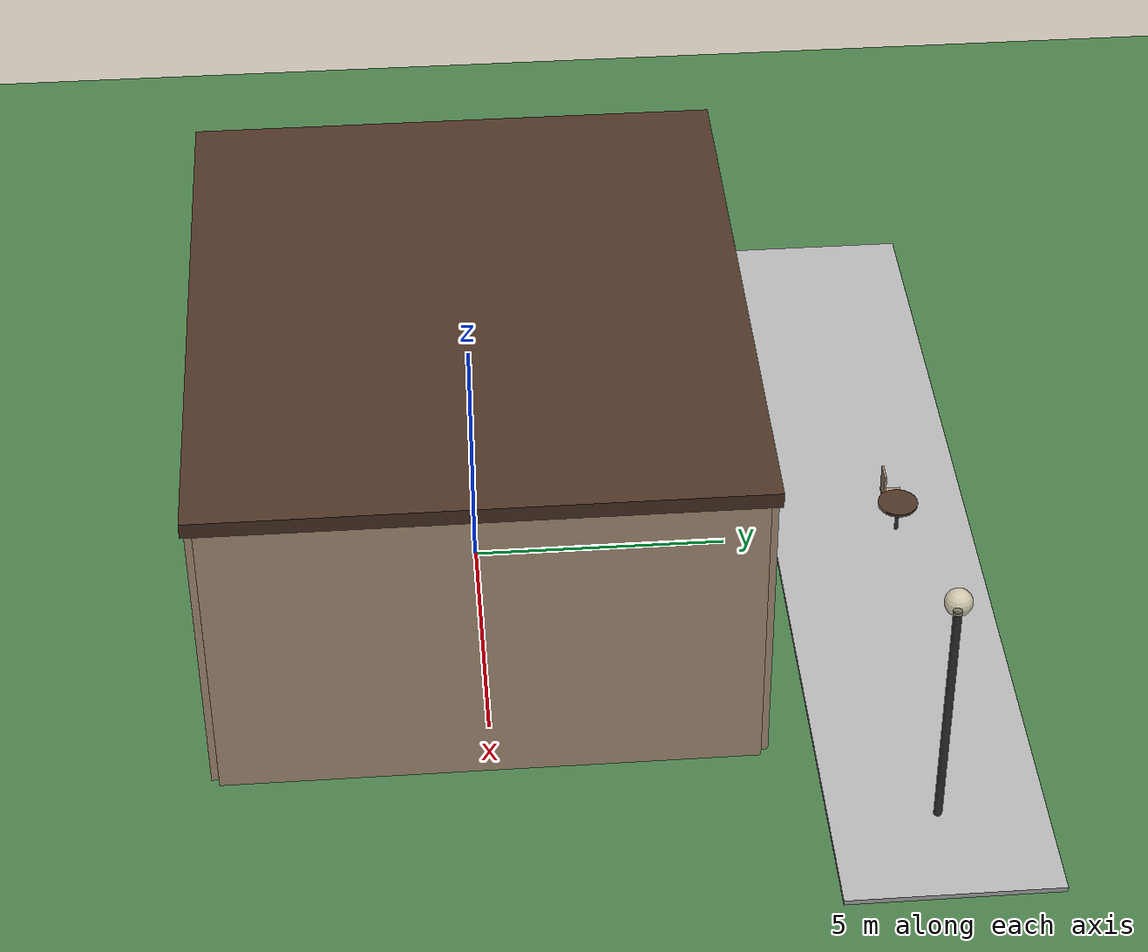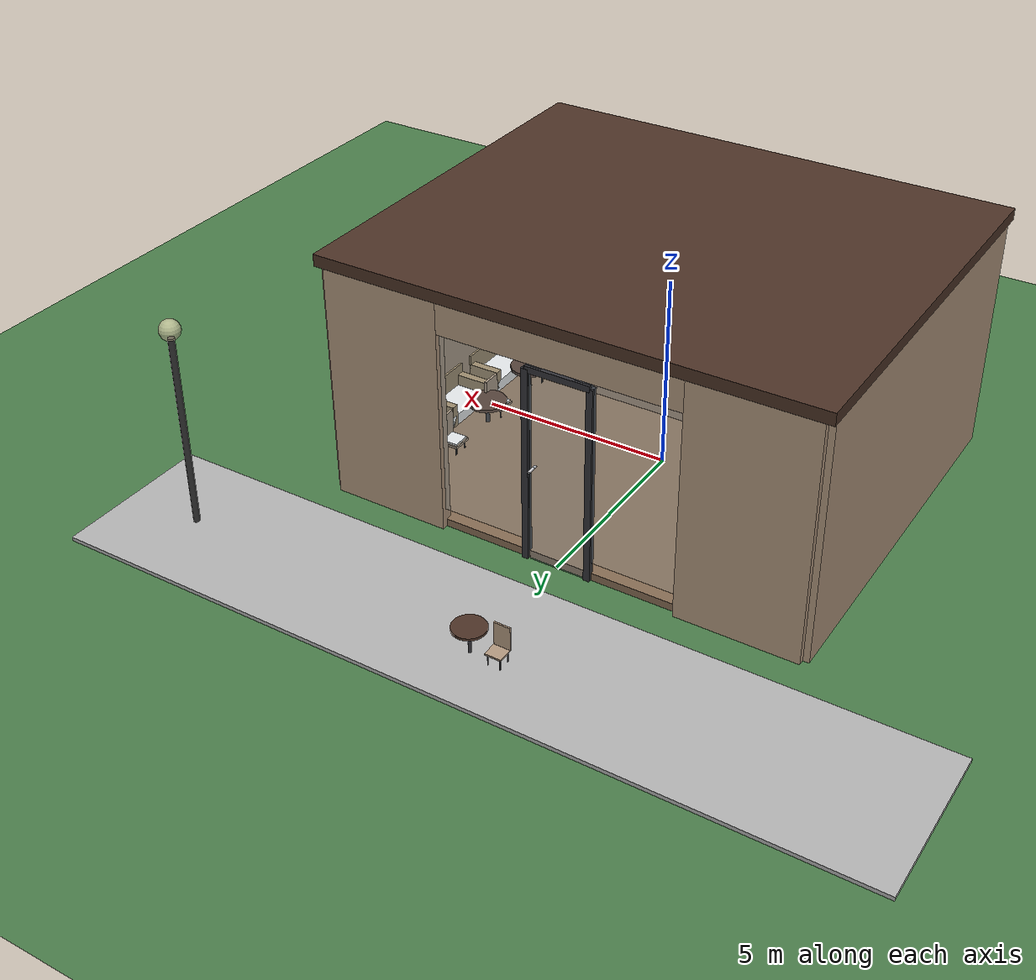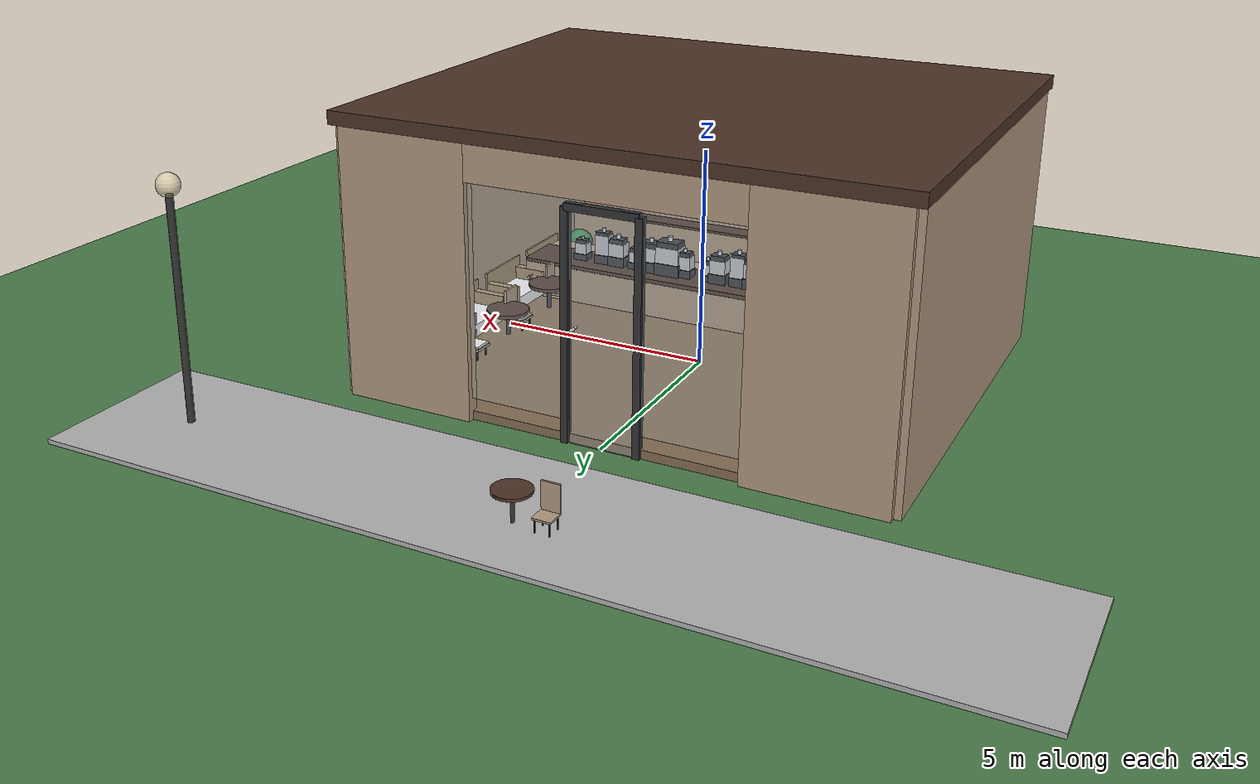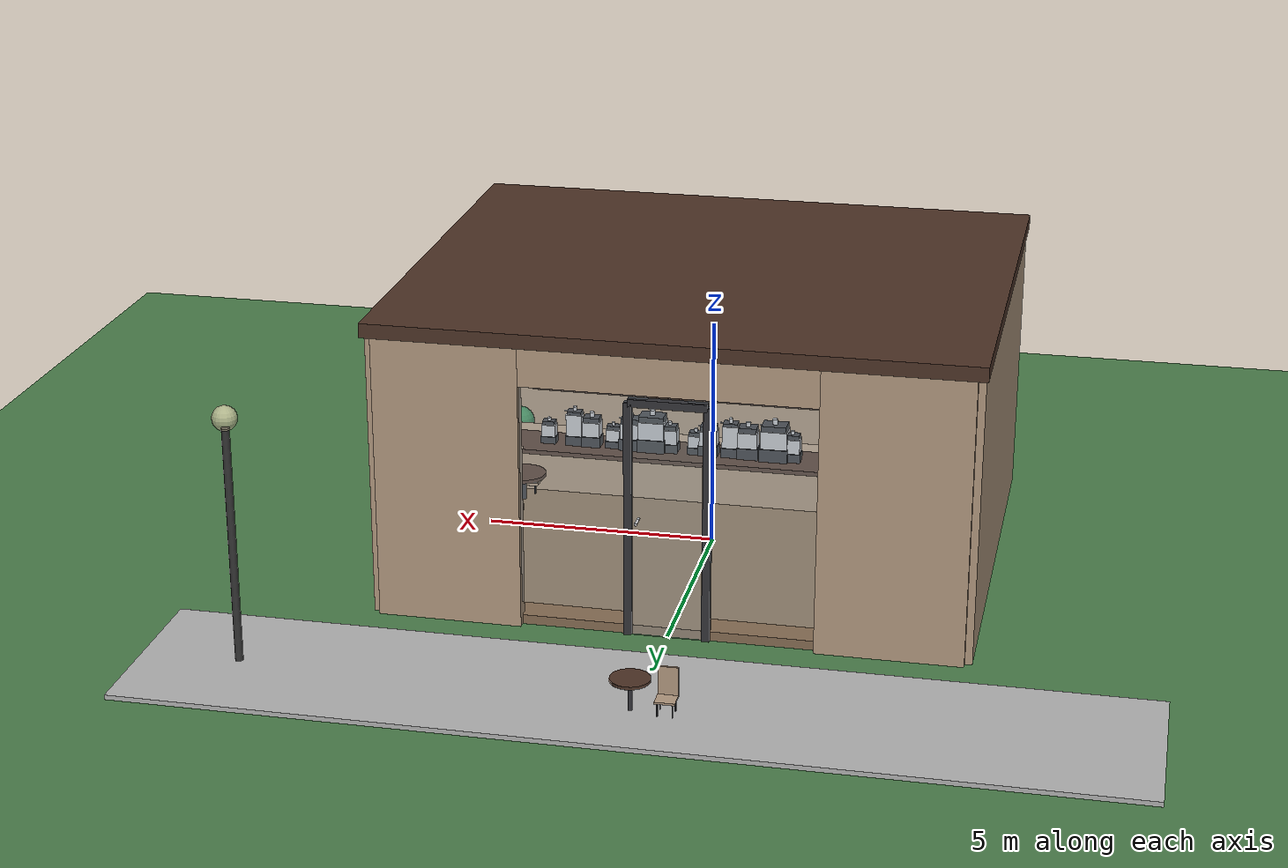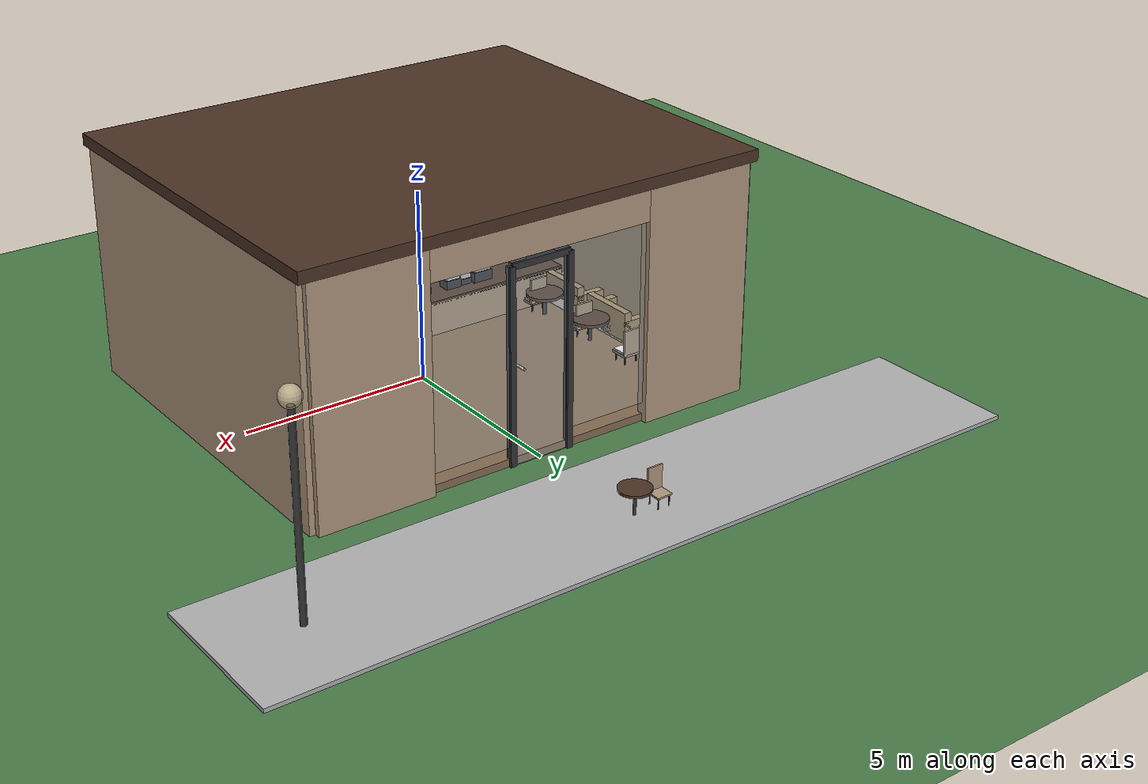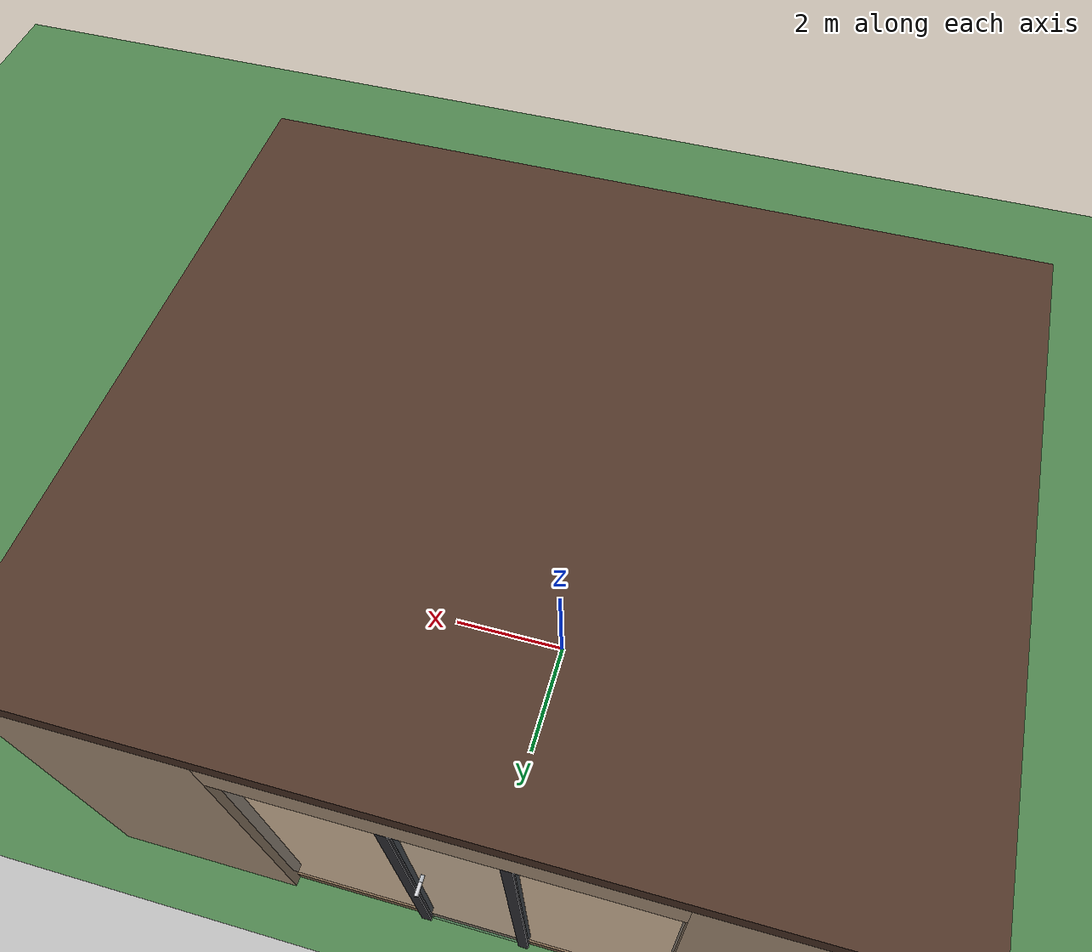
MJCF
<mujoco model="dynamic_glass_cafe">
  <!-- 编译器设置 -->
  <compiler angle="degree" coordinate="local" inertiafromgeom="true"/>

  <!-- 物理选项 -->
  <option timestep="0.005" gravity="0 0 -9.81" iterations="50" solver="Newton" tolerance="1e-10">
    <flag contact="enable" gravity="enable"/>
  </option>

  <!-- 默认设置 -->
  <default>
    <geom conaffinity="1" condim="3" friction="1 0.5 0.005" solimp="0.9 0.95 0.001" solref="0.02 1"/>
    <joint damping="0.5" armature="0.01"/>
    <motor ctrlrange="-1 1" ctrllimited="true"/>
  </default>

  <!-- 视觉设置 -->
  <visual>
    <map force="0.1" zfar="100"/>
    <rgba haze="0.05 0.08 0.12 1"/>
    <quality shadowsize="4096"/>
    <global offwidth="1280" offheight="720"/>
  </visual>

  <!-- 资源定义 -->
  <asset>
    <!-- 木地板 -->
    <texture name="wood_floor" type="2d" builtin="checker" rgb1="0.55 0.45 0.35" rgb2="0.5 0.4 0.3" width="512" height="512"/>
    <material name="wood_floor_mat" texture="wood_floor" texrepeat="10 10" specular="0.3" shininess="0.3" reflectance="0.1"/>

    <!-- 高透明玻璃 -->
    <material name="glass_clear" rgba="0.8 0.9 0.95 0.15" specular="1" shininess="1" reflectance="0.7"/>

    <!-- 半透明玻璃门 -->
    <material name="glass_door" rgba="0.75 0.85 0.9 0.25" specular="1" shininess="1" reflectance="0.6"/>

    <!-- 金属材质 -->
    <material name="metal_dark" rgba="0.2 0.2 0.22 1" specular="0.9" shininess="0.8" reflectance="0.4"/>
    <material name="metal_chrome" rgba="0.8 0.8 0.82 1" specular="1" shininess="0.9" reflectance="0.6"/>

    <!-- 木材 -->
    <material name="wood_dark" rgba="0.3 0.2 0.15 1" specular="0.2" shininess="0.2" reflectance="0"/>
    <material name="wood_light" rgba="0.7 0.6 0.5 1" specular="0.3" shininess="0.3" reflectance="0.05"/>
    <material name="wood_round" rgba="0.65 0.55 0.4 1" specular="0.25" shininess="0.25" reflectance="0.03"/>

    <!-- 布料 -->
    <material name="fabric_red" rgba="0.8 0.2 0.2 1" specular="0.1" shininess="0.1"/>
    <material name="fabric_blue" rgba="0.2 0.4 0.7 1" specular="0.1" shininess="0.1"/>
    <material name="fabric_beige" rgba="0.9 0.85 0.75 1" specular="0.1" shininess="0.1"/>
    <material name="fabric_light" rgba="0.95 0.93 0.9 1" specular="0.1" shininess="0.1"/>
    <material name="fabric_white" rgba="1 1 1 1" specular="0.1" shininess="0.1"/>

    <!-- 草地 -->
    <texture name="grass" type="2d" builtin="checker" rgb1="0.3 0.5 0.3" rgb2="0.28 0.48 0.28" width="512" height="512"/>
    <material name="grass_mat" texture="grass" texrepeat="40 40" specular="0.1" shininess="0.05" reflectance="0"/>

    <!-- 天空 -->
    <texture name="skybox" type="skybox" builtin="gradient" rgb1="0.6 0.75 0.9" rgb2="0.3 0.5 0.7" width="512" height="512"/>

    <!-- 菜单图片纹理 -->
    <texture name="menu_texture_1" type="2d" file="菜单1.png"/>
    <material name="menu_mat_1" texture="menu_texture_1" specular="0.1" shininess="0.1"/>
    <texture name="menu_texture_2" type="2d" file="菜单2.png"/>
    <material name="menu_mat_2" texture="menu_texture_2" specular="0.1" shininess="0.1"/>
    <texture name="menu_texture_3" type="2d" file="菜单3.png"/>
    <material name="menu_mat_3" texture="menu_texture_3" specular="0.1" shininess="0.1"/>
  </asset>

  <!-- 世界主体 -->
  <worldbody>
    <!-- 主光源（阳光 - 增强） -->
    <light directional="true" diffuse="1.2 1.2 1.1" specular="0.6 0.6 0.5" pos="30 20 40" dir="-1 -0.7 -1.5" castshadow="true"/>

    <!-- 辅助光源 - 增强 -->
    <light directional="true" diffuse="0.5 0.55 0.6" specular="0.3 0.3 0.3" pos="-20 -15 30" dir="0.7 0.5 -1" castshadow="false"/>

    <!-- 室内顶部光源 -->
    <light directional="false" diffuse="1.0 0.95 0.85" specular="0.4 0.4 0.3" pos="0 0 5.5" dir="0 0 -1" castshadow="false" cutoff="80"/>

    <!-- 地面 -->
    <geom name="ground" type="plane" size="50 50 0.1" material="grass_mat" condim="3" friction="1 0.5 0.005"/>

    <!-- ========== 咖啡店主体建筑 ========== -->
    <body name="cafe_building" pos="0 0 0">

      <!-- 地板 -->
      <geom name="cafe_floor" type="box" size="6 5 0.1" pos="0 0 0.1" material="wood_floor_mat"/>

      <!-- 后墙（实墙） -->
      <geom name="back_wall" type="box" size="6 0.15 3" pos="0 -5 3" material="wood_light"/>

      <!-- 左侧墙（实墙） -->
      <geom name="left_wall" type="box" size="0.15 5 3" pos="-6 0 3" material="wood_light"/>

      <!-- 左侧墙上的海报 -->
      <geom name="poster_left_1" type="box" size="0.01 0.8 1.0" pos="-5.9 2 3.5" rgba="0.9 0.85 0.7 1"/>
      <geom name="poster_left_2" type="box" size="0.01 0.8 1.0" pos="-5.9 0 3.5" rgba="0.85 0.8 0.75 1"/>
      <geom name="poster_left_3" type="box" size="0.01 0.8 1.0" pos="-5.9 -2 3.5" rgba="0.9 0.88 0.8 1"/>

      <!-- 右侧墙（实墙） -->
      <geom name="right_wall" type="box" size="0.15 5 3" pos="6 0 3" material="wood_light"/>

      <!-- 右侧墙上的海报 -->
      <geom name="poster_right_1" type="box" size="0.01 0.8 1.0" pos="5.9 2 3.5" rgba="0.85 0.8 0.75 1"/>
      <geom name="poster_right_2" type="box" size="0.01 0.8 1.0" pos="5.9 0 3.5" rgba="0.9 0.85 0.7 1"/>
      <geom name="poster_right_3" type="box" size="0.01 0.8 1.0" pos="5.9 -2 3.5" rgba="0.88 0.82 0.78 1"/>

      <!-- 前墙左侧（实墙部分） -->
      <geom name="front_wall_left" type="box" size="1.5 0.15 3" pos="-4.5 5 3" material="wood_light"/>

      <!-- 前墙右侧（实墙部分） -->
      <geom name="front_wall_right" type="box" size="1.5 0.15 3" pos="4.5 5 3" material="wood_light"/>

      <!-- 前墙顶部横梁 -->
      <geom name="front_beam_top" type="box" size="3 0.15 0.4" pos="0 5 5.6" material="wood_light"/>

      <!-- 大型透明玻璃窗 - 前面 -->
      <geom name="front_glass_left" type="box" size="1.3 0.02 2.5" pos="-1.7 5 3" material="glass_clear"/>
      <geom name="front_glass_right" type="box" size="1.3 0.02 2.5" pos="1.7 5 3" material="glass_clear"/>

      <!-- 透明玻璃窗 - 左侧 -->
      <geom name="left_glass_1" type="box" size="0.02 2 2" pos="-6 -2 3" material="glass_clear"/>
      <geom name="left_glass_2" type="box" size="0.02 1.5 2" pos="-6 2 3" material="glass_clear"/>

      <!-- 透明玻璃窗 - 右侧 -->
      <geom name="right_glass_1" type="box" size="0.02 2 2" pos="6 -2 3" material="glass_clear"/>
      <geom name="right_glass_2" type="box" size="0.02 1.5 2" pos="6 2 3" material="glass_clear"/>

      <!-- 屋顶 -->
      <geom name="roof" type="box" size="6.2 5.2 0.15" pos="0 0 6.15" material="wood_dark"/>

      <!-- 门框 -->
      <geom name="door_frame_left" type="box" size="0.08 0.08 2.5" pos="-0.8 5 2.5" material="metal_dark"/>
      <geom name="door_frame_right" type="box" size="0.08 0.08 2.5" pos="0.8 5 2.5" material="metal_dark"/>
      <geom name="door_frame_top" type="box" size="0.8 0.08 0.08" pos="0 5 5" material="metal_dark"/>

    </body>

    <!-- ========== 动态玻璃门（可开合） ========== -->
    <body name="glass_door" pos="0 5 2.5">
      <joint name="door_hinge" type="hinge" pos="-0.7 0 0" axis="0 0 1" range="-5 90" damping="3" stiffness="5"/>
      <geom name="door_glass" type="box" size="0.7 0.03 2.5" pos="0 0 0" material="glass_door"/>
      <geom name="door_handle" type="cylinder" size="0.03 0.15" pos="0.6 0.08 0" quat="0.707 0.707 0 0" material="metal_chrome"/>
    </body>

    <!-- ========== 吧台区域 ========== -->
    <!-- 吧台后墙架子 -->
    <body name="bar_shelves" pos="0 -3.5 0">
      <geom name="back_shelf_1" type="box" size="5.0 0.25 0.03" pos="0 -0.6 1.8" material="wood_dark"/>
      <geom name="back_shelf_2" type="box" size="5.0 0.25 0.03" pos="0 -0.6 2.5" material="wood_dark"/>
      <geom name="back_shelf_3" type="box" size="5.0 0.25 0.03" pos="0 -0.6 3.2" material="wood_dark"/>
    </body>

    <!-- 架子前面的大吧台 -->
    <body name="bar_counter" pos="0 -2.2 0">
      <!-- 吧台主体 -->
      <geom name="counter_top" type="box" size="5.5 0.6 0.05" pos="0 0 1.1" material="wood_dark"/>
      <geom name="counter_front" type="box" size="5.5 0.6 0.55" pos="0 0 0.55" material="wood_light"/>
      <geom name="counter_back" type="box" size="5.5 0.6 0.55" pos="0 -0.6 0.55" material="wood_light"/>

      <!-- 咖啡机1（意式咖啡机 - 最左侧） -->
      <geom name="coffee_machine_1_base" type="box" size="0.28 0.22 0.18" pos="-3.2 0 1.25" material="metal_dark"/>
      <geom name="coffee_machine_1_body" type="box" size="0.25 0.2 0.28" pos="-3.2 0 1.52" material="metal_chrome"/>
      <geom name="coffee_machine_1_top" type="box" size="0.22 0.18 0.08" pos="-3.2 0 1.85" material="metal_dark"/>
      <geom name="coffee_machine_1_group_head_l" type="cylinder" size="0.05 0.1" pos="-3.35 0 1.92" material="metal_chrome"/>
      <geom name="coffee_machine_1_group_head_r" type="cylinder" size="0.05 0.1" pos="-3.05 0 1.92" material="metal_chrome"/>
      <geom name="coffee_machine_1_steam_wand" type="cylinder" size="0.012 0.12" pos="-2.9 0 1.88" quat="0.707 0 0.707 0" material="metal_chrome"/>

      <!-- 咖啡机2（单头咖啡机） -->
      <geom name="coffee_machine_2_base" type="box" size="0.22 0.18 0.16" pos="-2.3 0 1.23" material="metal_dark"/>
      <geom name="coffee_machine_2_body" type="box" size="0.2 0.16 0.24" pos="-2.3 0 1.49" material="metal_chrome"/>
      <geom name="coffee_machine_2_top" type="box" size="0.18 0.14 0.06" pos="-2.3 0 1.78" material="metal_dark"/>
      <geom name="coffee_machine_2_group_head" type="cylinder" size="0.05 0.1" pos="-2.3 0 1.85" material="metal_chrome"/>
      <geom name="coffee_machine_2_steam_wand" type="cylinder" size="0.012 0.1" pos="-2.15 0 1.82" quat="0.707 0 0.707 0" material="metal_chrome"/>

      <!-- 咖啡机3（小型咖啡机） -->
      <geom name="coffee_machine_3_base" type="box" size="0.2 0.16 0.14" pos="-1.4 0 1.21" material="metal_dark"/>
      <geom name="coffee_machine_3_body" type="box" size="0.18 0.14 0.22" pos="-1.4 0 1.46" material="metal_chrome"/>
      <geom name="coffee_machine_3_top" type="box" size="0.16 0.12 0.05" pos="-1.4 0 1.73" material="metal_dark"/>
      <geom name="coffee_machine_3_group_head" type="cylinder" size="0.04 0.08" pos="-1.4 0 1.78" material="metal_chrome"/>
      <geom name="coffee_machine_3_steam_wand" type="cylinder" size="0.01 0.08" pos="-1.25 0 1.75" quat="0.707 0 0.707 0" material="metal_chrome"/>

      <!-- 咖啡机4（紧凑型咖啡机） -->
      <geom name="coffee_machine_4_base" type="box" size="0.24 0.2 0.17" pos="-0.4 0 1.24" material="metal_dark"/>
      <geom name="coffee_machine_4_body" type="box" size="0.22 0.18 0.26" pos="-0.4 0 1.51" material="metal_chrome"/>
      <geom name="coffee_machine_4_top" type="box" size="0.2 0.16 0.07" pos="-0.4 0 1.82" material="metal_dark"/>
      <geom name="coffee_machine_4_group_head" type="cylinder" size="0.05 0.1" pos="-0.4 0 1.89" material="metal_chrome"/>
      <geom name="coffee_machine_4_steam_wand" type="cylinder" size="0.012 0.11" pos="-0.25 0 1.86" quat="0.707 0 0.707 0" material="metal_chrome"/>

      <!-- 咖啡机5（紧凑型咖啡机） -->
      <geom name="coffee_machine_5_base" type="box" size="0.22 0.18 0.16" pos="0.5 0 1.23" material="metal_dark"/>
      <geom name="coffee_machine_5_body" type="box" size="0.2 0.16 0.24" pos="0.5 0 1.49" material="metal_chrome"/>
      <geom name="coffee_machine_5_top" type="box" size="0.18 0.14 0.06" pos="0.5 0 1.78" material="metal_dark"/>
      <geom name="coffee_machine_5_group_head" type="cylinder" size="0.05 0.1" pos="0.5 0 1.85" material="metal_chrome"/>
      <geom name="coffee_machine_5_steam_wand" type="cylinder" size="0.012 0.1" pos="0.65 0 1.82" quat="0.707 0 0.707 0" material="metal_chrome"/>

      <!-- 咖啡机6（小型咖啡机） -->
      <geom name="coffee_machine_6_base" type="box" size="0.2 0.16 0.14" pos="1.4 0 1.21" material="metal_dark"/>
      <geom name="coffee_machine_6_body" type="box" size="0.18 0.14 0.22" pos="1.4 0 1.46" material="metal_chrome"/>
      <geom name="coffee_machine_6_top" type="box" size="0.16 0.12 0.05" pos="1.4 0 1.73" material="metal_dark"/>
      <geom name="coffee_machine_6_group_head" type="cylinder" size="0.04 0.08" pos="1.4 0 1.78" material="metal_chrome"/>
      <geom name="coffee_machine_6_steam_wand" type="cylinder" size="0.01 0.08" pos="1.55 0 1.75" quat="0.707 0 0.707 0" material="metal_chrome"/>

      <!-- 咖啡机7（紧凑型咖啡机） -->
      <geom name="coffee_machine_7_base" type="box" size="0.24 0.2 0.17" pos="2.3 0 1.24" material="metal_dark"/>
      <geom name="coffee_machine_7_body" type="box" size="0.22 0.18 0.26" pos="2.3 0 1.51" material="metal_chrome"/>
      <geom name="coffee_machine_7_top" type="box" size="0.2 0.16 0.07" pos="2.3 0 1.82" material="metal_dark"/>
      <geom name="coffee_machine_7_group_head" type="cylinder" size="0.05 0.1" pos="2.3 0 1.89" material="metal_chrome"/>
      <geom name="coffee_machine_7_steam_wand" type="cylinder" size="0.012 0.11" pos="2.45 0 1.86" quat="0.707 0 0.707 0" material="metal_chrome"/>

      <!-- 咖啡机8（单头咖啡机） -->
      <geom name="coffee_machine_8_base" type="box" size="0.22 0.18 0.16" pos="3.2 0 1.23" material="metal_dark"/>
      <geom name="coffee_machine_8_body" type="box" size="0.2 0.16 0.24" pos="3.2 0 1.49" material="metal_chrome"/>
      <geom name="coffee_machine_8_top" type="box" size="0.18 0.14 0.06" pos="3.2 0 1.78" material="metal_dark"/>
      <geom name="coffee_machine_8_group_head" type="cylinder" size="0.05 0.1" pos="3.2 0 1.85" material="metal_chrome"/>
      <geom name="coffee_machine_8_steam_wand" type="cylinder" size="0.012 0.1" pos="3.35 0 1.82" quat="0.707 0 0.707 0" material="metal_chrome"/>

      <!-- 咖啡机9（超小型咖啡机） -->
      <geom name="coffee_machine_9_base" type="box" size="0.18 0.14 0.12" pos="-2.7 0 1.19" material="metal_dark"/>
      <geom name="coffee_machine_9_body" type="box" size="0.16 0.12 0.18" pos="-2.7 0 1.4" material="metal_chrome"/>
      <geom name="coffee_machine_9_top" type="box" size="0.14 0.1 0.04" pos="-2.7 0 1.63" material="metal_dark"/>
      <geom name="coffee_machine_9_group_head" type="cylinder" size="0.035 0.07" pos="-2.7 0 1.67" material="metal_chrome"/>

      <!-- 咖啡机10（宽型咖啡机） -->
      <geom name="coffee_machine_10_base" type="box" size="0.32 0.24 0.19" pos="-1.0 0 1.26" material="metal_dark"/>
      <geom name="coffee_machine_10_body" type="box" size="0.3 0.22 0.3" pos="-1.0 0 1.56" material="metal_chrome"/>
      <geom name="coffee_machine_10_top" type="box" size="0.28 0.2 0.08" pos="-1.0 0 1.91" material="metal_dark"/>
      <geom name="coffee_machine_10_group_head" type="cylinder" size="0.06 0.12" pos="-1.0 0 1.99" material="metal_chrome"/>
      <geom name="coffee_machine_10_steam_wand" type="cylinder" size="0.014 0.13" pos="-0.8 0 1.95" quat="0.707 0 0.707 0" material="metal_chrome"/>

      <!-- 咖啡机11（高型咖啡机） -->
      <geom name="coffee_machine_11_base" type="box" size="0.2 0.16 0.15" pos="0.0 0 1.22" material="metal_dark"/>
      <geom name="coffee_machine_11_body" type="box" size="0.18 0.14 0.32" pos="0.0 0 1.56" material="metal_chrome"/>
      <geom name="coffee_machine_11_top" type="box" size="0.16 0.12 0.06" pos="0.0 0 1.89" material="metal_dark"/>
      <geom name="coffee_machine_11_group_head" type="cylinder" size="0.045 0.09" pos="0.0 0 1.96" material="metal_chrome"/>
      <geom name="coffee_machine_11_steam_wand" type="cylinder" size="0.011 0.09" pos="0.15 0 1.93" quat="0.707 0 0.707 0" material="metal_chrome"/>

      <!-- 咖啡机12（超小型咖啡机） -->
      <geom name="coffee_machine_12_base" type="box" size="0.18 0.14 0.12" pos="0.8 0 1.19" material="metal_dark"/>
      <geom name="coffee_machine_12_body" type="box" size="0.16 0.12 0.18" pos="0.8 0 1.4" material="metal_chrome"/>
      <geom name="coffee_machine_12_top" type="box" size="0.14 0.1 0.04" pos="0.8 0 1.63" material="metal_dark"/>
      <geom name="coffee_machine_12_group_head" type="cylinder" size="0.035 0.07" pos="0.8 0 1.67" material="metal_chrome"/>

      <!-- 咖啡机13（宽型咖啡机） -->
      <geom name="coffee_machine_13_base" type="box" size="0.32 0.24 0.19" pos="1.8 0 1.26" material="metal_dark"/>
      <geom name="coffee_machine_13_body" type="box" size="0.3 0.22 0.3" pos="1.8 0 1.56" material="metal_chrome"/>
      <geom name="coffee_machine_13_top" type="box" size="0.28 0.2 0.08" pos="1.8 0 1.91" material="metal_dark"/>
      <geom name="coffee_machine_13_group_head" type="cylinder" size="0.06 0.12" pos="1.8 0 1.99" material="metal_chrome"/>
      <geom name="coffee_machine_13_steam_wand" type="cylinder" size="0.014 0.13" pos="2.0 0 1.95" quat="0.707 0 0.707 0" material="metal_chrome"/>

      <!-- 咖啡机14（超小型咖啡机） -->
      <geom name="coffee_machine_14_base" type="box" size="0.18 0.14 0.12" pos="2.7 0 1.19" material="metal_dark"/>
      <geom name="coffee_machine_14_body" type="box" size="0.16 0.12 0.18" pos="2.7 0 1.4" material="metal_chrome"/>
      <geom name="coffee_machine_14_top" type="box" size="0.14 0.1 0.04" pos="2.7 0 1.63" material="metal_dark"/>
      <geom name="coffee_machine_14_group_head" type="cylinder" size="0.035 0.07" pos="2.7 0 1.67" material="metal_chrome"/>

      <!-- 咖啡机15（高型咖啡机） -->
      <geom name="coffee_machine_15_base" type="box" size="0.2 0.16 0.15" pos="3.6 0 1.22" material="metal_dark"/>
      <geom name="coffee_machine_15_body" type="box" size="0.18 0.14 0.32" pos="3.6 0 1.56" material="metal_chrome"/>
      <geom name="coffee_machine_15_top" type="box" size="0.16 0.12 0.06" pos="3.6 0 1.89" material="metal_dark"/>
      <geom name="coffee_machine_15_group_head" type="cylinder" size="0.045 0.09" pos="3.6 0 1.96" material="metal_chrome"/>
      <geom name="coffee_machine_15_steam_wand" type="cylinder" size="0.011 0.09" pos="3.75 0 1.93" quat="0.707 0 0.707 0" material="metal_chrome"/>

      <!-- 咖啡机16（超小型咖啡机 - 最右侧） -->
      <geom name="coffee_machine_16_base" type="box" size="0.18 0.14 0.12" pos="4.2 0 1.19" material="metal_dark"/>
      <geom name="coffee_machine_16_body" type="box" size="0.16 0.12 0.18" pos="4.2 0 1.4" material="metal_chrome"/>
      <geom name="coffee_machine_16_top" type="box" size="0.14 0.1 0.04" pos="4.2 0 1.63" material="metal_dark"/>
      <geom name="coffee_machine_16_group_head" type="cylinder" size="0.035 0.07" pos="4.2 0 1.67" material="metal_chrome"/>

      <!-- 咖啡杯（放在吧台上） -->
      <geom name="cup_1" type="cylinder" size="0.04 0.08" pos="-0.5 0 1.23" material="fabric_beige"/>
      <geom name="cup_2" type="cylinder" size="0.04 0.08" pos="-0.2 0 1.23" material="fabric_beige"/>
      <geom name="cup_3" type="cylinder" size="0.04 0.08" pos="0.1 0 1.23" material="fabric_beige"/>

      <!-- 架子上的果汁瓶子 - 第1层（修复悬空，添加不同形状） -->
      <!-- 架子1表面在z=1.83，瓶子底部应放在此高度 -->
      <!-- 圆形瓶子 -->
      <geom name="juice_bottle_1_base" type="cylinder" size="0.055 0.04" pos="-3.5 -0.55 1.87" rgba="0.85 0.9 0.95 0.25"/>
      <geom name="juice_bottle_1_body" type="cylinder" size="0.05 0.15" pos="-3.5 -0.55 2.02" rgba="0.8 0.85 0.9 0.2"/>
      <geom name="juice_bottle_1_neck" type="cylinder" size="0.025 0.05" pos="-3.5 -0.55 2.22" rgba="0.85 0.9 0.95 0.25"/>
      <geom name="juice_bottle_1_liquid" type="cylinder" size="0.045 0.13" pos="-3.5 -0.55 2.0" rgba="0.9 0.5 0.1 0.7"/>

      <!-- 方形瓶子1 -->
      <geom name="juice_bottle_sq1_base" type="box" size="0.05 0.05 0.04" pos="-3.0 -0.55 1.87" rgba="0.85 0.9 0.95 0.25"/>
      <geom name="juice_bottle_sq1_body" type="box" size="0.045 0.045 0.15" pos="-3.0 -0.55 2.02" rgba="0.8 0.85 0.9 0.2"/>
      <geom name="juice_bottle_sq1_neck" type="box" size="0.02 0.02 0.05" pos="-3.0 -0.55 2.22" rgba="0.85 0.9 0.95 0.25"/>
      <geom name="juice_bottle_sq1_liquid" type="box" size="0.04 0.04 0.13" pos="-3.0 -0.55 2.0" rgba="0.8 0.9 0.3 0.7"/>

      <!-- 圆形瓶子2 -->
      <geom name="juice_bottle_2_base" type="cylinder" size="0.055 0.04" pos="-2.5 -0.55 1.87" rgba="0.85 0.9 0.95 0.25"/>
      <geom name="juice_bottle_2_body" type="cylinder" size="0.05 0.15" pos="-2.5 -0.55 2.02" rgba="0.8 0.85 0.9 0.2"/>
      <geom name="juice_bottle_2_neck" type="cylinder" size="0.025 0.05" pos="-2.5 -0.55 2.22" rgba="0.85 0.9 0.95 0.25"/>
      <geom name="juice_bottle_2_liquid" type="cylinder" size="0.045 0.13" pos="-2.5 -0.55 2.0" rgba="0.6 0.2 0.5 0.7"/>

      <!-- 高瘦圆形瓶子 -->
      <geom name="juice_bottle_tall1_base" type="cylinder" size="0.045 0.04" pos="-2.0 -0.55 1.87" rgba="0.85 0.9 0.95 0.25"/>
      <geom name="juice_bottle_tall1_body" type="cylinder" size="0.04 0.18" pos="-2.0 -0.55 2.05" rgba="0.8 0.85 0.9 0.2"/>
      <geom name="juice_bottle_tall1_neck" type="cylinder" size="0.02 0.06" pos="-2.0 -0.55 2.29" rgba="0.85 0.9 0.95 0.25"/>
      <geom name="juice_bottle_tall1_liquid" type="cylinder" size="0.035 0.16" pos="-2.0 -0.55 2.03" rgba="0.95 0.9 0.3 0.7"/>

      <!-- 方形瓶子2 -->
      <geom name="juice_bottle_sq2_base" type="box" size="0.05 0.05 0.04" pos="-1.5 -0.55 1.87" rgba="0.85 0.9 0.95 0.25"/>
      <geom name="juice_bottle_sq2_body" type="box" size="0.045 0.045 0.15" pos="-1.5 -0.55 2.02" rgba="0.8 0.85 0.9 0.2"/>
      <geom name="juice_bottle_sq2_neck" type="box" size="0.02 0.02 0.05" pos="-1.5 -0.55 2.22" rgba="0.85 0.9 0.95 0.25"/>
      <geom name="juice_bottle_sq2_liquid" type="box" size="0.04 0.04 0.13" pos="-1.5 -0.55 2.0" rgba="0.9 0.3 0.4 0.7"/>

      <!-- 圆形瓶子3 -->
      <geom name="juice_bottle_3_base" type="cylinder" size="0.055 0.04" pos="-1.0 -0.55 1.87" rgba="0.85 0.9 0.95 0.25"/>
      <geom name="juice_bottle_3_body" type="cylinder" size="0.05 0.15" pos="-1.0 -0.55 2.02" rgba="0.8 0.85 0.9 0.2"/>
      <geom name="juice_bottle_3_neck" type="cylinder" size="0.025 0.05" pos="-1.0 -0.55 2.22" rgba="0.85 0.9 0.95 0.25"/>
      <geom name="juice_bottle_3_liquid" type="cylinder" size="0.045 0.13" pos="-1.0 -0.55 2.0" rgba="0.4 0.7 0.5 0.7"/>

      <!-- 宽圆形瓶子 -->
      <geom name="juice_bottle_wide1_base" type="cylinder" size="0.065 0.04" pos="-0.5 -0.55 1.87" rgba="0.85 0.9 0.95 0.25"/>
      <geom name="juice_bottle_wide1_body" type="cylinder" size="0.06 0.12" pos="-0.5 -0.55 1.99" rgba="0.8 0.85 0.9 0.2"/>
      <geom name="juice_bottle_wide1_neck" type="cylinder" size="0.025 0.05" pos="-0.5 -0.55 2.17" rgba="0.85 0.9 0.95 0.25"/>
      <geom name="juice_bottle_wide1_liquid" type="cylinder" size="0.055 0.10" pos="-0.5 -0.55 1.97" rgba="0.6 0.8 0.4 0.7"/>

      <!-- 圆形瓶子4 -->
      <geom name="juice_bottle_4_base" type="cylinder" size="0.055 0.04" pos="0.0 -0.55 1.87" rgba="0.85 0.9 0.95 0.25"/>
      <geom name="juice_bottle_4_body" type="cylinder" size="0.05 0.15" pos="0.0 -0.55 2.02" rgba="0.8 0.85 0.9 0.2"/>
      <geom name="juice_bottle_4_neck" type="cylinder" size="0.025 0.05" pos="0.0 -0.55 2.22" rgba="0.85 0.9 0.95 0.25"/>
      <geom name="juice_bottle_4_liquid" type="cylinder" size="0.045 0.13" pos="0.0 -0.55 2.0" rgba="0.5 0.5 0.7 0.7"/>

      <!-- 方形瓶子3 -->
      <geom name="juice_bottle_sq3_base" type="box" size="0.05 0.05 0.04" pos="0.5 -0.55 1.87" rgba="0.85 0.9 0.95 0.25"/>
      <geom name="juice_bottle_sq3_body" type="box" size="0.045 0.045 0.15" pos="0.5 -0.55 2.02" rgba="0.8 0.85 0.9 0.2"/>
      <geom name="juice_bottle_sq3_neck" type="box" size="0.02 0.02 0.05" pos="0.5 -0.55 2.22" rgba="0.85 0.9 0.95 0.25"/>
      <geom name="juice_bottle_sq3_liquid" type="box" size="0.04 0.04 0.13" pos="0.5 -0.55 2.0" rgba="0.7 0.4 0.6 0.7"/>

      <!-- 圆形瓶子5 -->
      <geom name="juice_bottle_5_base" type="cylinder" size="0.055 0.04" pos="1.0 -0.55 1.87" rgba="0.85 0.9 0.95 0.25"/>
      <geom name="juice_bottle_5_body" type="cylinder" size="0.05 0.15" pos="1.0 -0.55 2.02" rgba="0.8 0.85 0.9 0.2"/>
      <geom name="juice_bottle_5_neck" type="cylinder" size="0.025 0.05" pos="1.0 -0.55 2.22" rgba="0.85 0.9 0.95 0.25"/>
      <geom name="juice_bottle_5_liquid" type="cylinder" size="0.045 0.13" pos="1.0 -0.55 2.0" rgba="0.8 0.5 0.3 0.7"/>

      <!-- 高瘦圆形瓶子2 -->
      <geom name="juice_bottle_tall2_base" type="cylinder" size="0.045 0.04" pos="1.5 -0.55 1.87" rgba="0.85 0.9 0.95 0.25"/>
      <geom name="juice_bottle_tall2_body" type="cylinder" size="0.04 0.18" pos="1.5 -0.55 2.05" rgba="0.8 0.85 0.9 0.2"/>
      <geom name="juice_bottle_tall2_neck" type="cylinder" size="0.02 0.06" pos="1.5 -0.55 2.29" rgba="0.85 0.9 0.95 0.25"/>
      <geom name="juice_bottle_tall2_liquid" type="cylinder" size="0.035 0.16" pos="1.5 -0.55 2.03" rgba="0.9 0.4 0.5 0.7"/>

      <!-- 圆形瓶子6 -->
      <geom name="juice_bottle_6_base" type="cylinder" size="0.055 0.04" pos="2.0 -0.55 1.87" rgba="0.85 0.9 0.95 0.25"/>
      <geom name="juice_bottle_6_body" type="cylinder" size="0.05 0.15" pos="2.0 -0.55 2.02" rgba="0.8 0.85 0.9 0.2"/>
      <geom name="juice_bottle_6_neck" type="cylinder" size="0.025 0.05" pos="2.0 -0.55 2.22" rgba="0.85 0.9 0.95 0.25"/>
      <geom name="juice_bottle_6_liquid" type="cylinder" size="0.045 0.13" pos="2.0 -0.55 2.0" rgba="0.7 0.6 0.3 0.7"/>

      <!-- 方形瓶子4 -->
      <geom name="juice_bottle_sq4_base" type="box" size="0.05 0.05 0.04" pos="2.5 -0.55 1.87" rgba="0.85 0.9 0.95 0.25"/>
      <geom name="juice_bottle_sq4_body" type="box" size="0.045 0.045 0.15" pos="2.5 -0.55 2.02" rgba="0.8 0.85 0.9 0.2"/>
      <geom name="juice_bottle_sq4_neck" type="box" size="0.02 0.02 0.05" pos="2.5 -0.55 2.22" rgba="0.85 0.9 0.95 0.25"/>
      <geom name="juice_bottle_sq4_liquid" type="box" size="0.04 0.04 0.13" pos="2.5 -0.55 2.0" rgba="0.6 0.5 0.4 0.7"/>

      <!-- 圆形瓶子7 -->
      <geom name="juice_bottle_7_base" type="cylinder" size="0.055 0.04" pos="3.0 -0.55 1.87" rgba="0.85 0.9 0.95 0.25"/>
      <geom name="juice_bottle_7_body" type="cylinder" size="0.05 0.15" pos="3.0 -0.55 2.02" rgba="0.8 0.85 0.9 0.2"/>
      <geom name="juice_bottle_7_neck" type="cylinder" size="0.025 0.05" pos="3.0 -0.55 2.22" rgba="0.85 0.9 0.95 0.25"/>
      <geom name="juice_bottle_7_liquid" type="cylinder" size="0.045 0.13" pos="3.0 -0.55 2.0" rgba="0.5 0.4 0.5 0.7"/>

      <!-- 宽圆形瓶子2 -->
      <geom name="juice_bottle_wide2_base" type="cylinder" size="0.065 0.04" pos="3.5 -0.55 1.87" rgba="0.85 0.9 0.95 0.25"/>
      <geom name="juice_bottle_wide2_body" type="cylinder" size="0.06 0.12" pos="3.5 -0.55 1.99" rgba="0.8 0.85 0.9 0.2"/>
      <geom name="juice_bottle_wide2_neck" type="cylinder" size="0.025 0.05" pos="3.5 -0.55 2.17" rgba="0.85 0.9 0.95 0.25"/>
      <geom name="juice_bottle_wide2_liquid" type="cylinder" size="0.055 0.10" pos="3.5 -0.55 1.97" rgba="0.4 0.5 0.6 0.7"/>

      <!-- 架子上的果汁瓶子 - 第2层（修复悬空，添加不同形状） -->
      <!-- 架子2表面在z=2.53，瓶子底部应放在此高度 -->
      <!-- 圆形瓶子 -->
      <geom name="juice_bottle_l2_1_base" type="cylinder" size="0.055 0.04" pos="-3.5 -0.55 2.57" rgba="0.85 0.9 0.95 0.25"/>
      <geom name="juice_bottle_l2_1_body" type="cylinder" size="0.05 0.15" pos="-3.5 -0.55 2.72" rgba="0.8 0.85 0.9 0.2"/>
      <geom name="juice_bottle_l2_1_neck" type="cylinder" size="0.025 0.05" pos="-3.5 -0.55 2.92" rgba="0.85 0.9 0.95 0.25"/>
      <geom name="juice_bottle_l2_1_liquid" type="cylinder" size="0.045 0.13" pos="-3.5 -0.55 2.7" rgba="0.3 0.2 0.6 0.7"/>

      <!-- 方形瓶子 -->
      <geom name="juice_bottle_l2_sq1_base" type="box" size="0.05 0.05 0.04" pos="-3.0 -0.55 2.57" rgba="0.85 0.9 0.95 0.25"/>
      <geom name="juice_bottle_l2_sq1_body" type="box" size="0.045 0.045 0.15" pos="-3.0 -0.55 2.72" rgba="0.8 0.85 0.9 0.2"/>
      <geom name="juice_bottle_l2_sq1_neck" type="box" size="0.02 0.02 0.05" pos="-3.0 -0.55 2.92" rgba="0.85 0.9 0.95 0.25"/>
      <geom name="juice_bottle_l2_sq1_liquid" type="box" size="0.04 0.04 0.13" pos="-3.0 -0.55 2.7" rgba="0.9 0.6 0.2 0.7"/>

      <!-- 圆形瓶子 -->
      <geom name="juice_bottle_l2_2_base" type="cylinder" size="0.055 0.04" pos="-2.5 -0.55 2.57" rgba="0.85 0.9 0.95 0.25"/>
      <geom name="juice_bottle_l2_2_body" type="cylinder" size="0.05 0.15" pos="-2.5 -0.55 2.72" rgba="0.8 0.85 0.9 0.2"/>
      <geom name="juice_bottle_l2_2_neck" type="cylinder" size="0.025 0.05" pos="-2.5 -0.55 2.92" rgba="0.85 0.9 0.95 0.25"/>
      <geom name="juice_bottle_l2_2_liquid" type="cylinder" size="0.045 0.13" pos="-2.5 -0.55 2.7" rgba="0.9 0.2 0.2 0.7"/>

      <!-- 高瘦圆形瓶子 -->
      <geom name="juice_bottle_l2_tall1_base" type="cylinder" size="0.045 0.04" pos="-2.0 -0.55 2.57" rgba="0.85 0.9 0.95 0.25"/>
      <geom name="juice_bottle_l2_tall1_body" type="cylinder" size="0.04 0.18" pos="-2.0 -0.55 2.75" rgba="0.8 0.85 0.9 0.2"/>
      <geom name="juice_bottle_l2_tall1_neck" type="cylinder" size="0.02 0.06" pos="-2.0 -0.55 2.99" rgba="0.85 0.9 0.95 0.25"/>
      <geom name="juice_bottle_l2_tall1_liquid" type="cylinder" size="0.035 0.16" pos="-2.0 -0.55 2.73" rgba="0.95 0.85 0.3 0.7"/>

      <!-- 方形瓶子 -->
      <geom name="juice_bottle_l2_sq2_base" type="box" size="0.05 0.05 0.04" pos="-1.5 -0.55 2.57" rgba="0.85 0.9 0.95 0.25"/>
      <geom name="juice_bottle_l2_sq2_body" type="box" size="0.045 0.045 0.15" pos="-1.5 -0.55 2.72" rgba="0.8 0.85 0.9 0.2"/>
      <geom name="juice_bottle_l2_sq2_neck" type="box" size="0.02 0.02 0.05" pos="-1.5 -0.55 2.92" rgba="0.85 0.9 0.95 0.25"/>
      <geom name="juice_bottle_l2_sq2_liquid" type="box" size="0.04 0.04 0.13" pos="-1.5 -0.55 2.7" rgba="0.95 0.7 0.6 0.7"/>

      <!-- 圆形瓶子 -->
      <geom name="juice_bottle_l2_3_base" type="cylinder" size="0.055 0.04" pos="-1.0 -0.55 2.57" rgba="0.85 0.9 0.95 0.25"/>
      <geom name="juice_bottle_l2_3_body" type="cylinder" size="0.05 0.15" pos="-1.0 -0.55 2.72" rgba="0.8 0.85 0.9 0.2"/>
      <geom name="juice_bottle_l2_3_neck" type="cylinder" size="0.025 0.05" pos="-1.0 -0.55 2.92" rgba="0.85 0.9 0.95 0.25"/>
      <geom name="juice_bottle_l2_3_liquid" type="cylinder" size="0.045 0.13" pos="-1.0 -0.55 2.7" rgba="0.8 0.5 0.3 0.7"/>

      <!-- 宽圆形瓶子 -->
      <geom name="juice_bottle_l2_wide1_base" type="cylinder" size="0.065 0.04" pos="-0.5 -0.55 2.57" rgba="0.85 0.9 0.95 0.25"/>
      <geom name="juice_bottle_l2_wide1_body" type="cylinder" size="0.06 0.12" pos="-0.5 -0.55 2.69" rgba="0.8 0.85 0.9 0.2"/>
      <geom name="juice_bottle_l2_wide1_neck" type="cylinder" size="0.025 0.05" pos="-0.5 -0.55 2.87" rgba="0.85 0.9 0.95 0.25"/>
      <geom name="juice_bottle_l2_wide1_liquid" type="cylinder" size="0.055 0.10" pos="-0.5 -0.55 2.67" rgba="0.9 0.4 0.5 0.7"/>

      <!-- 圆形瓶子 -->
      <geom name="juice_bottle_l2_4_base" type="cylinder" size="0.055 0.04" pos="0.0 -0.55 2.57" rgba="0.85 0.9 0.95 0.25"/>
      <geom name="juice_bottle_l2_4_body" type="cylinder" size="0.05 0.15" pos="0.0 -0.55 2.72" rgba="0.8 0.85 0.9 0.2"/>
      <geom name="juice_bottle_l2_4_neck" type="cylinder" size="0.025 0.05" pos="0.0 -0.55 2.92" rgba="0.85 0.9 0.95 0.25"/>
      <geom name="juice_bottle_l2_4_liquid" type="cylinder" size="0.045 0.13" pos="0.0 -0.55 2.7" rgba="0.7 0.6 0.3 0.7"/>

      <!-- 方形瓶子 -->
      <geom name="juice_bottle_l2_sq3_base" type="box" size="0.05 0.05 0.04" pos="0.5 -0.55 2.57" rgba="0.85 0.9 0.95 0.25"/>
      <geom name="juice_bottle_l2_sq3_body" type="box" size="0.045 0.045 0.15" pos="0.5 -0.55 2.72" rgba="0.8 0.85 0.9 0.2"/>
      <geom name="juice_bottle_l2_sq3_neck" type="box" size="0.02 0.02 0.05" pos="0.5 -0.55 2.92" rgba="0.85 0.9 0.95 0.25"/>
      <geom name="juice_bottle_l2_sq3_liquid" type="box" size="0.04 0.04 0.13" pos="0.5 -0.55 2.7" rgba="0.6 0.5 0.4 0.7"/>

      <!-- 圆形瓶子 -->
      <geom name="juice_bottle_l2_5_base" type="cylinder" size="0.055 0.04" pos="1.0 -0.55 2.57" rgba="0.85 0.9 0.95 0.25"/>
      <geom name="juice_bottle_l2_5_body" type="cylinder" size="0.05 0.15" pos="1.0 -0.55 2.72" rgba="0.8 0.85 0.9 0.2"/>
      <geom name="juice_bottle_l2_5_neck" type="cylinder" size="0.025 0.05" pos="1.0 -0.55 2.92" rgba="0.85 0.9 0.95 0.25"/>
      <geom name="juice_bottle_l2_5_liquid" type="cylinder" size="0.045 0.13" pos="1.0 -0.55 2.7" rgba="0.5 0.4 0.5 0.7"/>

      <!-- 高瘦圆形瓶子 -->
      <geom name="juice_bottle_l2_tall2_base" type="cylinder" size="0.045 0.04" pos="1.5 -0.55 2.57" rgba="0.85 0.9 0.95 0.25"/>
      <geom name="juice_bottle_l2_tall2_body" type="cylinder" size="0.04 0.18" pos="1.5 -0.55 2.75" rgba="0.8 0.85 0.9 0.2"/>
      <geom name="juice_bottle_l2_tall2_neck" type="cylinder" size="0.02 0.06" pos="1.5 -0.55 2.99" rgba="0.85 0.9 0.95 0.25"/>
      <geom name="juice_bottle_l2_tall2_liquid" type="cylinder" size="0.035 0.16" pos="1.5 -0.55 2.73" rgba="0.4 0.5 0.6 0.7"/>

      <!-- 圆形瓶子 -->
      <geom name="juice_bottle_l2_6_base" type="cylinder" size="0.055 0.04" pos="2.0 -0.55 2.57" rgba="0.85 0.9 0.95 0.25"/>
      <geom name="juice_bottle_l2_6_body" type="cylinder" size="0.05 0.15" pos="2.0 -0.55 2.72" rgba="0.8 0.85 0.9 0.2"/>
      <geom name="juice_bottle_l2_6_neck" type="cylinder" size="0.025 0.05" pos="2.0 -0.55 2.92" rgba="0.85 0.9 0.95 0.25"/>
      <geom name="juice_bottle_l2_6_liquid" type="cylinder" size="0.045 0.13" pos="2.0 -0.55 2.7" rgba="0.3 0.5 0.6 0.7"/>

      <!-- 方形瓶子 -->
      <geom name="juice_bottle_l2_sq4_base" type="box" size="0.05 0.05 0.04" pos="2.5 -0.55 2.57" rgba="0.85 0.9 0.95 0.25"/>
      <geom name="juice_bottle_l2_sq4_body" type="box" size="0.045 0.045 0.15" pos="2.5 -0.55 2.72" rgba="0.8 0.85 0.9 0.2"/>
      <geom name="juice_bottle_l2_sq4_neck" type="box" size="0.02 0.02 0.05" pos="2.5 -0.55 2.92" rgba="0.85 0.9 0.95 0.25"/>
      <geom name="juice_bottle_l2_sq4_liquid" type="box" size="0.04 0.04 0.13" pos="2.5 -0.55 2.7" rgba="0.2 0.4 0.5 0.7"/>

      <!-- 圆形瓶子 -->
      <geom name="juice_bottle_l2_7_base" type="cylinder" size="0.055 0.04" pos="3.0 -0.55 2.57" rgba="0.85 0.9 0.95 0.25"/>
      <geom name="juice_bottle_l2_7_body" type="cylinder" size="0.05 0.15" pos="3.0 -0.55 2.72" rgba="0.8 0.85 0.9 0.2"/>
      <geom name="juice_bottle_l2_7_neck" type="cylinder" size="0.025 0.05" pos="3.0 -0.55 2.92" rgba="0.85 0.9 0.95 0.25"/>
      <geom name="juice_bottle_l2_7_liquid" type="cylinder" size="0.045 0.13" pos="3.0 -0.55 2.7" rgba="0.1 0.3 0.4 0.7"/>

      <!-- 宽圆形瓶子 -->
      <geom name="juice_bottle_l2_wide2_base" type="cylinder" size="0.065 0.04" pos="3.5 -0.55 2.57" rgba="0.85 0.9 0.95 0.25"/>
      <geom name="juice_bottle_l2_wide2_body" type="cylinder" size="0.06 0.12" pos="3.5 -0.55 2.69" rgba="0.8 0.85 0.9 0.2"/>
      <geom name="juice_bottle_l2_wide2_neck" type="cylinder" size="0.025 0.05" pos="3.5 -0.55 2.87" rgba="0.85 0.9 0.95 0.25"/>
      <geom name="juice_bottle_l2_wide2_liquid" type="cylinder" size="0.055 0.10" pos="3.5 -0.55 2.67" rgba="0.05 0.2 0.3 0.7"/>

      <!-- 架子上的果汁瓶子 - 第3层（修复悬空，添加不同形状） -->
      <!-- 架子3表面在z=3.23，瓶子底部应放在此高度 -->
      <!-- 圆形瓶子 -->
      <geom name="juice_bottle_l3_1_base" type="cylinder" size="0.055 0.04" pos="-3.5 -0.55 3.27" rgba="0.85 0.9 0.95 0.25"/>
      <geom name="juice_bottle_l3_1_body" type="cylinder" size="0.05 0.15" pos="-3.5 -0.55 3.42" rgba="0.8 0.85 0.9 0.2"/>
      <geom name="juice_bottle_l3_1_neck" type="cylinder" size="0.025 0.05" pos="-3.5 -0.55 3.62" rgba="0.85 0.9 0.95 0.25"/>
      <geom name="juice_bottle_l3_1_liquid" type="cylinder" size="0.045 0.13" pos="-3.5 -0.55 3.4" rgba="0.8 0.4 0.3 0.7"/>

      <!-- 方形瓶子 -->
      <geom name="juice_bottle_l3_sq1_base" type="box" size="0.05 0.05 0.04" pos="-3.0 -0.55 3.27" rgba="0.85 0.9 0.95 0.25"/>
      <geom name="juice_bottle_l3_sq1_body" type="box" size="0.045 0.045 0.15" pos="-3.0 -0.55 3.42" rgba="0.8 0.85 0.9 0.2"/>
      <geom name="juice_bottle_l3_sq1_neck" type="box" size="0.02 0.02 0.05" pos="-3.0 -0.55 3.62" rgba="0.85 0.9 0.95 0.25"/>
      <geom name="juice_bottle_l3_sq1_liquid" type="box" size="0.04 0.04 0.13" pos="-3.0 -0.55 3.4" rgba="0.7 0.5 0.4 0.7"/>

      <!-- 圆形瓶子 -->
      <geom name="juice_bottle_l3_2_base" type="cylinder" size="0.055 0.04" pos="-2.5 -0.55 3.27" rgba="0.85 0.9 0.95 0.25"/>
      <geom name="juice_bottle_l3_2_body" type="cylinder" size="0.05 0.15" pos="-2.5 -0.55 3.42" rgba="0.8 0.85 0.9 0.2"/>
      <geom name="juice_bottle_l3_2_neck" type="cylinder" size="0.025 0.05" pos="-2.5 -0.55 3.62" rgba="0.85 0.9 0.95 0.25"/>
      <geom name="juice_bottle_l3_2_liquid" type="cylinder" size="0.045 0.13" pos="-2.5 -0.55 3.4" rgba="0.6 0.7 0.3 0.7"/>

      <!-- 高瘦圆形瓶子 -->
      <geom name="juice_bottle_l3_tall1_base" type="cylinder" size="0.045 0.04" pos="-2.0 -0.55 3.27" rgba="0.85 0.9 0.95 0.25"/>
      <geom name="juice_bottle_l3_tall1_body" type="cylinder" size="0.04 0.18" pos="-2.0 -0.55 3.45" rgba="0.8 0.85 0.9 0.2"/>
      <geom name="juice_bottle_l3_tall1_neck" type="cylinder" size="0.02 0.06" pos="-2.0 -0.55 3.69" rgba="0.85 0.9 0.95 0.25"/>
      <geom name="juice_bottle_l3_tall1_liquid" type="cylinder" size="0.035 0.16" pos="-2.0 -0.55 3.43" rgba="0.5 0.6 0.4 0.7"/>

      <!-- 方形瓶子 -->
      <geom name="juice_bottle_l3_sq2_base" type="box" size="0.05 0.05 0.04" pos="-1.5 -0.55 3.27" rgba="0.85 0.9 0.95 0.25"/>
      <geom name="juice_bottle_l3_sq2_body" type="box" size="0.045 0.045 0.15" pos="-1.5 -0.55 3.42" rgba="0.8 0.85 0.9 0.2"/>
      <geom name="juice_bottle_l3_sq2_neck" type="box" size="0.02 0.02 0.05" pos="-1.5 -0.55 3.62" rgba="0.85 0.9 0.95 0.25"/>
      <geom name="juice_bottle_l3_sq2_liquid" type="box" size="0.04 0.04 0.13" pos="-1.5 -0.55 3.4" rgba="0.4 0.5 0.5 0.7"/>

      <!-- 圆形瓶子 -->
      <geom name="juice_bottle_l3_3_base" type="cylinder" size="0.055 0.04" pos="-1.0 -0.55 3.27" rgba="0.85 0.9 0.95 0.25"/>
      <geom name="juice_bottle_l3_3_body" type="cylinder" size="0.05 0.15" pos="-1.0 -0.55 3.42" rgba="0.8 0.85 0.9 0.2"/>
      <geom name="juice_bottle_l3_3_neck" type="cylinder" size="0.025 0.05" pos="-1.0 -0.55 3.62" rgba="0.85 0.9 0.95 0.25"/>
      <geom name="juice_bottle_l3_3_liquid" type="cylinder" size="0.045 0.13" pos="-1.0 -0.55 3.4" rgba="0.3 0.4 0.5 0.7"/>

      <!-- 宽圆形瓶子 -->
      <geom name="juice_bottle_l3_wide1_base" type="cylinder" size="0.065 0.04" pos="-0.5 -0.55 3.27" rgba="0.85 0.9 0.95 0.25"/>
      <geom name="juice_bottle_l3_wide1_body" type="cylinder" size="0.06 0.12" pos="-0.5 -0.55 3.39" rgba="0.8 0.85 0.9 0.2"/>
      <geom name="juice_bottle_l3_wide1_neck" type="cylinder" size="0.025 0.05" pos="-0.5 -0.55 3.57" rgba="0.85 0.9 0.95 0.25"/>
      <geom name="juice_bottle_l3_wide1_liquid" type="cylinder" size="0.055 0.10" pos="-0.5 -0.55 3.37" rgba="0.2 0.3 0.4 0.7"/>

      <!-- 圆形瓶子 -->
      <geom name="juice_bottle_l3_4_base" type="cylinder" size="0.055 0.04" pos="0.0 -0.55 3.27" rgba="0.85 0.9 0.95 0.25"/>
      <geom name="juice_bottle_l3_4_body" type="cylinder" size="0.05 0.15" pos="0.0 -0.55 3.42" rgba="0.8 0.85 0.9 0.2"/>
      <geom name="juice_bottle_l3_4_neck" type="cylinder" size="0.025 0.05" pos="0.0 -0.55 3.62" rgba="0.85 0.9 0.95 0.25"/>
      <geom name="juice_bottle_l3_4_liquid" type="cylinder" size="0.045 0.13" pos="0.0 -0.55 3.4" rgba="0.1 0.2 0.3 0.7"/>

      <!-- 方形瓶子 -->
      <geom name="juice_bottle_l3_sq3_base" type="box" size="0.05 0.05 0.04" pos="0.5 -0.55 3.27" rgba="0.85 0.9 0.95 0.25"/>
      <geom name="juice_bottle_l3_sq3_body" type="box" size="0.045 0.045 0.15" pos="0.5 -0.55 3.42" rgba="0.8 0.85 0.9 0.2"/>
      <geom name="juice_bottle_l3_sq3_neck" type="box" size="0.02 0.02 0.05" pos="0.5 -0.55 3.62" rgba="0.85 0.9 0.95 0.25"/>
      <geom name="juice_bottle_l3_sq3_liquid" type="box" size="0.04 0.04 0.13" pos="0.5 -0.55 3.4" rgba="0.05 0.15 0.25 0.7"/>

      <!-- 圆形瓶子 -->
      <geom name="juice_bottle_l3_5_base" type="cylinder" size="0.055 0.04" pos="1.0 -0.55 3.27" rgba="0.85 0.9 0.95 0.25"/>
      <geom name="juice_bottle_l3_5_body" type="cylinder" size="0.05 0.15" pos="1.0 -0.55 3.42" rgba="0.8 0.85 0.9 0.2"/>
      <geom name="juice_bottle_l3_5_neck" type="cylinder" size="0.025 0.05" pos="1.0 -0.55 3.62" rgba="0.85 0.9 0.95 0.25"/>
      <geom name="juice_bottle_l3_5_liquid" type="cylinder" size="0.045 0.13" pos="1.0 -0.55 3.4" rgba="0.8 0.3 0.2 0.7"/>

      <!-- 高瘦圆形瓶子 -->
      <geom name="juice_bottle_l3_tall2_base" type="cylinder" size="0.045 0.04" pos="1.5 -0.55 3.27" rgba="0.85 0.9 0.95 0.25"/>
      <geom name="juice_bottle_l3_tall2_body" type="cylinder" size="0.04 0.18" pos="1.5 -0.55 3.45" rgba="0.8 0.85 0.9 0.2"/>
      <geom name="juice_bottle_l3_tall2_neck" type="cylinder" size="0.02 0.06" pos="1.5 -0.55 3.69" rgba="0.85 0.9 0.95 0.25"/>
      <geom name="juice_bottle_l3_tall2_liquid" type="cylinder" size="0.035 0.16" pos="1.5 -0.55 3.43" rgba="0.7 0.2 0.1 0.7"/>

      <!-- 圆形瓶子 -->
      <geom name="juice_bottle_l3_6_base" type="cylinder" size="0.055 0.04" pos="2.0 -0.55 3.27" rgba="0.85 0.9 0.95 0.25"/>
      <geom name="juice_bottle_l3_6_body" type="cylinder" size="0.05 0.15" pos="2.0 -0.55 3.42" rgba="0.8 0.85 0.9 0.2"/>
      <geom name="juice_bottle_l3_6_neck" type="cylinder" size="0.025 0.05" pos="2.0 -0.55 3.62" rgba="0.85 0.9 0.95 0.25"/>
      <geom name="juice_bottle_l3_6_liquid" type="cylinder" size="0.045 0.13" pos="2.0 -0.55 3.4" rgba="0.6 0.1 0.05 0.7"/>

      <!-- 方形瓶子 -->
      <geom name="juice_bottle_l3_sq4_base" type="box" size="0.05 0.05 0.04" pos="2.5 -0.55 3.27" rgba="0.85 0.9 0.95 0.25"/>
      <geom name="juice_bottle_l3_sq4_body" type="box" size="0.045 0.045 0.15" pos="2.5 -0.55 3.42" rgba="0.8 0.85 0.9 0.2"/>
      <geom name="juice_bottle_l3_sq4_neck" type="box" size="0.02 0.02 0.05" pos="2.5 -0.55 3.62" rgba="0.85 0.9 0.95 0.25"/>
      <geom name="juice_bottle_l3_sq4_liquid" type="box" size="0.04 0.04 0.13" pos="2.5 -0.55 3.4" rgba="0.5 0.05 0.02 0.7"/>

      <!-- 圆形瓶子 -->
      <geom name="juice_bottle_l3_7_base" type="cylinder" size="0.055 0.04" pos="3.0 -0.55 3.27" rgba="0.85 0.9 0.95 0.25"/>
      <geom name="juice_bottle_l3_7_body" type="cylinder" size="0.05 0.15" pos="3.0 -0.55 3.42" rgba="0.8 0.85 0.9 0.2"/>
      <geom name="juice_bottle_l3_7_neck" type="cylinder" size="0.025 0.05" pos="3.0 -0.55 3.62" rgba="0.85 0.9 0.95 0.25"/>
      <geom name="juice_bottle_l3_7_liquid" type="cylinder" size="0.045 0.13" pos="3.0 -0.55 3.4" rgba="0.4 0.05 0.01 0.7"/>

      <!-- 宽圆形瓶子 -->
      <geom name="juice_bottle_l3_wide2_base" type="cylinder" size="0.065 0.04" pos="3.5 -0.55 3.27" rgba="0.85 0.9 0.95 0.25"/>
      <geom name="juice_bottle_l3_wide2_body" type="cylinder" size="0.06 0.12" pos="3.5 -0.55 3.39" rgba="0.8 0.85 0.9 0.2"/>
      <geom name="juice_bottle_l3_wide2_neck" type="cylinder" size="0.025 0.05" pos="3.5 -0.55 3.57" rgba="0.85 0.9 0.95 0.25"/>
      <geom name="juice_bottle_l3_wide2_liquid" type="cylinder" size="0.055 0.10" pos="3.5 -0.55 3.37" rgba="0.3 0.02 0.005 0.7"/>

      <!-- 架子上方的菜单（使用图片纹理） -->
      <geom name="menu_board_1" type="box" size="0.7 0.5 0.02" pos="-2.5 -0.6 3.8" quat="0.707 0.707 0 0" material="menu_mat_1"/>
      <geom name="menu_board_1_frame" type="box" size="0.72 0.52 0.01" pos="-2.5 -0.6 3.82" quat="0.707 0.707 0 0" rgba="0.9 0.9 0.9 1"/>
      <geom name="menu_board_2" type="box" size="0.7 0.5 0.02" pos="0 -0.6 3.8" quat="0.707 0.707 0 0" material="menu_mat_2"/>
      <geom name="menu_board_2_frame" type="box" size="0.72 0.52 0.01" pos="0 -0.6 3.82" quat="0.707 0.707 0 0" rgba="0.9 0.9 0.9 1"/>
      <geom name="menu_board_3" type="box" size="0.7 0.5 0.02" pos="2.5 -0.6 3.8" quat="0.707 0.707 0 0" material="menu_mat_3"/>
      <geom name="menu_board_3_frame" type="box" size="0.72 0.52 0.01" pos="2.5 -0.6 3.82" quat="0.707 0.707 0 0" rgba="0.9 0.9 0.9 1"/>

      <!-- 吧台内部灯光 -->
      <light mode="fixed" directional="false" diffuse="1 0.9 0.7" specular="0.5 0.4 0.3" pos="0 -0.3 3" dir="0 0 -1" castshadow="false" cutoff="45"/>
    </body>

    <!-- ========== 天花板旋转风扇（动态，连接到天花板） ========== -->
    <body name="ceiling_fan" pos="0 0 6.15">
      <!-- 连接杆（连接到天花板） -->
      <geom name="fan_rod" type="cylinder" size="0.08 0.35" pos="0 0 -0.35" material="metal_dark"/>
      <!-- 底座 -->
      <geom name="fan_mount" type="cylinder" size="0.15 0.15" pos="0 0 -0.7" material="metal_dark"/>

      <!-- 旋转部分 -->
      <body name="fan_rotor" pos="0 0 -0.85">
        <joint name="fan_rotation" type="hinge" axis="0 0 1" damping="0.1"/>
        <geom name="fan_center" type="cylinder" size="0.12 0.05" pos="0 0 0" material="metal_chrome"/>

        <!-- 扇叶1 -->
        <geom name="fan_blade_1" type="box" size="0.6 0.12 0.02" pos="0 0 0" material="wood_light"/>
        <!-- 扇叶2 -->
        <geom name="fan_blade_2" type="box" size="0.6 0.12 0.02" pos="0 0 0" quat="0.866 0 0 0.5" material="wood_light"/>
        <!-- 扇叶3 -->
        <geom name="fan_blade_3" type="box" size="0.6 0.12 0.02" pos="0 0 0" quat="0.5 0 0 0.866" material="wood_light"/>
      </body>
    </body>

    <!-- ========== 摆钟（动态） ========== -->
    <body name="wall_clock" pos="0 -4.85 4.5">
      <!-- 钟面 -->
      <geom name="clock_face" type="cylinder" size="0.25 0.05" pos="0 0 0" quat="0.707 0.707 0 0" material="wood_light"/>
      <geom name="clock_center" type="cylinder" size="0.22 0.03" pos="0 -0.06 0" quat="0.707 0.707 0 0" rgba="1 1 1 1"/>

      <!-- 钟摆 -->
      <body name="pendulum" pos="0 -0.1 -0.3">
        <joint name="pendulum_swing" type="hinge" axis="1 0 0" range="-25 25" damping="0.05" stiffness="0.5"/>
        <geom name="pendulum_rod" type="cylinder" size="0.01 0.4" pos="0 0 -0.4" material="metal_dark"/>
        <geom name="pendulum_weight" type="sphere" size="0.08" pos="0 0 -0.8" material="metal_chrome"/>
      </body>
    </body>

    <!-- ========== 吊灯（连接到天花板） ========== -->
    <body name="pendant_lamp_1" pos="-2.5 1 6.15">
      <!-- 吊线（从天花板垂下，固定连接） -->
      <geom name="lamp1_cord" type="cylinder" size="0.01 0.65" pos="0 0 -0.65" material="metal_dark"/>
      <!-- 灯罩 -->
      <geom name="lamp1_shade" type="sphere" size="0.2" pos="0 0 -1.3" rgba="0.9 0.85 0.7 0.8"/>
      <!-- 灯光 -->
      <light mode="fixed" directional="false" diffuse="1 0.85 0.6" specular="0.4 0.3 0.2" pos="0 0 -1.3" dir="0 0 -1" castshadow="false" cutoff="50"/>
    </body>

    <body name="pendant_lamp_2" pos="2.5 1 6.15">
      <!-- 吊线（从天花板垂下，固定连接） -->
      <geom name="lamp2_cord" type="cylinder" size="0.01 0.65" pos="0 0 -0.65" material="metal_dark"/>
      <!-- 灯罩 -->
      <geom name="lamp2_shade" type="sphere" size="0.2" pos="0 0 -1.3" rgba="0.9 0.85 0.7 0.8"/>
      <!-- 灯光 -->
      <light mode="fixed" directional="false" diffuse="1 0.85 0.6" specular="0.4 0.3 0.2" pos="0 0 -1.3" dir="0 0 -1" castshadow="false" cutoff="50"/>
    </body>

    <!-- ========== 桌椅组合 ========== -->
    <!-- 左右两面墙各有三套桌椅，沙发靠墙，椅子背朝桌子，沙发背朝椅子 -->

    <!-- ========== 左墙（x=-6）三套桌椅 ========== -->
    <!-- 桌子1（左墙第1套） - 圆桌 -->
    <body name="table_1" pos="-4.5 -3 0">
      <geom name="table1_top" type="cylinder" size="0.5 0.04" pos="0 0 0.8" material="wood_dark"/>
      <geom name="table1_leg" type="cylinder" size="0.05 0.4" pos="0 0 0.4" material="metal_dark"/>
    </body>

    <!-- 桌子1的沙发（靠左墙，背朝椅子） -->
    <body name="sofa_1" pos="-5.5 -3 0" quat="0.707 0 0 0.707">
      <geom name="sofa1_seat" type="box" size="0.8 0.5 0.15" pos="0 0 0.4" material="fabric_white"/>
      <geom name="sofa1_back" type="box" size="0.8 0.1 0.4" pos="0 -0.4 0.7" material="wood_round"/>
      <geom name="sofa1_arm_left" type="box" size="0.1 0.5 0.3" pos="-0.7 0 0.55" material="wood_round"/>
      <geom name="sofa1_arm_right" type="box" size="0.1 0.5 0.3" pos="0.7 0 0.55" material="wood_round"/>
    </body>

    <!-- 桌子1的椅子（在桌子右侧，背朝桌子） -->
    <body name="chair_1_1" pos="-4.5 -1.5 0.45" quat="1 0 0 0">
      <geom name="chair1_1_seat" type="box" size="0.25 0.25 0.03" pos="0 0 0" material="wood_light"/>
      <geom name="chair1_1_back" type="box" size="0.25 0.03 0.35" pos="0 0.22 0.35" material="wood_light"/>
      <geom name="chair1_1_leg1" type="cylinder" size="0.02 0.225" pos="-0.18 -0.18 -0.225" material="metal_dark"/>
      <geom name="chair1_1_leg2" type="cylinder" size="0.02 0.225" pos="0.18 -0.18 -0.225" material="metal_dark"/>
      <geom name="chair1_1_leg3" type="cylinder" size="0.02 0.225" pos="-0.18 0.18 -0.225" material="metal_dark"/>
      <geom name="chair1_1_leg4" type="cylinder" size="0.02 0.225" pos="0.18 0.18 -0.225" material="metal_dark"/>
      <geom name="chair1_1_cushion" type="box" size="0.22 0.22 0.04" pos="0 0 0.04" material="fabric_white"/>
    </body>

    <!-- 桌子2（左墙第2套） - 圆桌 -->
    <body name="table_2" pos="-4.5 -1 0">
      <geom name="table2_top" type="cylinder" size="0.5 0.04" pos="0 0 0.8" material="wood_dark"/>
      <geom name="table2_leg" type="cylinder" size="0.05 0.4" pos="0 0 0.4" material="metal_dark"/>
    </body>

    <!-- 桌子2的沙发（靠左墙，背朝椅子） -->
    <body name="sofa_2" pos="-5.5 -1 0" quat="0.707 0 0 0.707">
      <geom name="sofa2_seat" type="box" size="0.8 0.5 0.15" pos="0 0 0.4" material="fabric_white"/>
      <geom name="sofa2_back" type="box" size="0.8 0.1 0.4" pos="0 -0.4 0.7" material="wood_round"/>
      <geom name="sofa2_arm_left" type="box" size="0.1 0.5 0.3" pos="-0.7 0 0.55" material="wood_round"/>
      <geom name="sofa2_arm_right" type="box" size="0.1 0.5 0.3" pos="0.7 0 0.55" material="wood_round"/>
    </body>

    <!-- 桌子2的椅子（在桌子右侧，背朝桌子） -->
    <body name="chair_2_1" pos="-4.5 0.5 0.45" quat="1 0 0 0">
      <geom name="chair2_1_seat" type="box" size="0.25 0.25 0.03" pos="0 0 0" material="wood_light"/>
      <geom name="chair2_1_back" type="box" size="0.25 0.03 0.35" pos="0 0.22 0.35" material="wood_light"/>
      <geom name="chair2_1_leg1" type="cylinder" size="0.02 0.225" pos="-0.18 -0.18 -0.225" material="metal_dark"/>
      <geom name="chair2_1_leg2" type="cylinder" size="0.02 0.225" pos="0.18 -0.18 -0.225" material="metal_dark"/>
      <geom name="chair2_1_leg3" type="cylinder" size="0.02 0.225" pos="-0.18 0.18 -0.225" material="metal_dark"/>
      <geom name="chair2_1_leg4" type="cylinder" size="0.02 0.225" pos="0.18 0.18 -0.225" material="metal_dark"/>
      <geom name="chair2_1_cushion" type="box" size="0.22 0.22 0.04" pos="0 0 0.04" material="fabric_white"/>
    </body>

    <!-- 桌子3（左墙第3套） - 圆桌 -->
    <body name="table_3" pos="-4.5 1 0">
      <geom name="table3_top" type="cylinder" size="0.5 0.04" pos="0 0 0.8" material="wood_dark"/>
      <geom name="table3_leg" type="cylinder" size="0.05 0.4" pos="0 0 0.4" material="metal_dark"/>
    </body>

    <!-- 桌子3的沙发（靠左墙，背朝椅子） -->
    <body name="sofa_3" pos="-5.5 1 0" quat="0.707 0 0 0.707">
      <geom name="sofa3_seat" type="box" size="0.8 0.5 0.15" pos="0 0 0.4" material="fabric_white"/>
      <geom name="sofa3_back" type="box" size="0.8 0.1 0.4" pos="0 -0.4 0.7" material="wood_round"/>
      <geom name="sofa3_arm_left" type="box" size="0.1 0.5 0.3" pos="-0.7 0 0.55" material="wood_round"/>
      <geom name="sofa3_arm_right" type="box" size="0.1 0.5 0.3" pos="0.7 0 0.55" material="wood_round"/>
    </body>

    <!-- 桌子3的椅子（在桌子右侧，背朝桌子） -->
    <body name="chair_3_1" pos="-4.5 2.5 0.45" quat="1 0 0 0">
      <geom name="chair3_1_seat" type="box" size="0.25 0.25 0.03" pos="0 0 0" material="wood_light"/>
      <geom name="chair3_1_back" type="box" size="0.25 0.03 0.35" pos="0 0.22 0.35" material="wood_light"/>
      <geom name="chair3_1_leg1" type="cylinder" size="0.02 0.225" pos="-0.18 -0.18 -0.225" material="metal_dark"/>
      <geom name="chair3_1_leg2" type="cylinder" size="0.02 0.225" pos="0.18 -0.18 -0.225" material="metal_dark"/>
      <geom name="chair3_1_leg3" type="cylinder" size="0.02 0.225" pos="-0.18 0.18 -0.225" material="metal_dark"/>
      <geom name="chair3_1_leg4" type="cylinder" size="0.02 0.225" pos="0.18 0.18 -0.225" material="metal_dark"/>
      <geom name="chair3_1_cushion" type="box" size="0.22 0.22 0.04" pos="0 0 0.04" material="fabric_white"/>
    </body>

    <!-- ========== 右墙（x=6）三套桌椅 ========== -->
    <!-- 桌子4（右墙第1套） - 圆桌 -->
    <body name="table_4" pos="4.5 -3 0">
      <geom name="table4_top" type="cylinder" size="0.5 0.04" pos="0 0 0.8" material="wood_dark"/>
      <geom name="table4_leg" type="cylinder" size="0.05 0.4" pos="0 0 0.4" material="metal_dark"/>
    </body>

    <!-- 桌子4的沙发（靠右墙，背朝椅子） -->
    <body name="sofa_4" pos="5.5 -3 0" quat="0.707 0 0 -0.707">
      <geom name="sofa4_seat" type="box" size="0.8 0.5 0.15" pos="0 0 0.4" material="fabric_white"/>
      <geom name="sofa4_back" type="box" size="0.8 0.1 0.4" pos="0 0.4 0.7" material="wood_round"/>
      <geom name="sofa4_arm_left" type="box" size="0.1 0.5 0.3" pos="-0.7 0 0.55" material="wood_round"/>
      <geom name="sofa4_arm_right" type="box" size="0.1 0.5 0.3" pos="0.7 0 0.55" material="wood_round"/>
    </body>

    <!-- 桌子4的椅子（在桌子左侧，背朝桌子） -->
    <body name="chair_4_1" pos="4.5 -1.5 0.45" quat="1 0 0 1">
      <geom name="chair4_1_seat" type="box" size="0.25 0.25 0.03" pos="0 0 0" material="wood_light"/>
      <geom name="chair4_1_back" type="box" size="0.25 0.03 0.35" pos="0 -0.22 0.35" material="wood_light"/>
      <geom name="chair4_1_leg1" type="cylinder" size="0.02 0.225" pos="-0.18 -0.18 -0.225" material="metal_dark"/>
      <geom name="chair4_1_leg2" type="cylinder" size="0.02 0.225" pos="0.18 -0.18 -0.225" material="metal_dark"/>
      <geom name="chair4_1_leg3" type="cylinder" size="0.02 0.225" pos="-0.18 0.18 -0.225" material="metal_dark"/>
      <geom name="chair4_1_leg4" type="cylinder" size="0.02 0.225" pos="0.18 0.18 -0.225" material="metal_dark"/>
      <geom name="chair4_1_cushion" type="box" size="0.22 0.22 0.04" pos="0 0 0.04" material="fabric_white"/>
    </body>

    <!-- 桌子5（右墙第2套） - 圆桌 -->
    <body name="table_5" pos="4.5 -1 0">
      <geom name="table5_top" type="cylinder" size="0.5 0.04" pos="0 0 0.8" material="wood_dark"/>
      <geom name="table5_leg" type="cylinder" size="0.05 0.4" pos="0 0 0.4" material="metal_dark"/>
    </body>

    <!-- 桌子5的沙发（靠右墙，背朝椅子） -->
    <body name="sofa_5" pos="5.5 -1 0" quat="0.707 0 0 -0.707">
      <geom name="sofa5_seat" type="box" size="0.8 0.5 0.15" pos="0 0 0.4" material="fabric_white"/>
      <geom name="sofa5_back" type="box" size="0.8 0.1 0.4" pos="0 0.4 0.7" material="wood_round"/>
      <geom name="sofa5_arm_left" type="box" size="0.1 0.5 0.3" pos="-0.7 0 0.55" material="wood_round"/>
      <geom name="sofa5_arm_right" type="box" size="0.1 0.5 0.3" pos="0.7 0 0.55" material="wood_round"/>
    </body>

    <!-- 桌子5的椅子（在桌子左侧，背朝桌子） -->
    <body name="chair_5_1" pos="4.5 0.5 0.45" quat="1 0 0 1">
      <geom name="chair5_1_seat" type="box" size="0.25 0.25 0.03" pos="0 0 0" material="wood_light"/>
      <geom name="chair5_1_back" type="box" size="0.25 0.03 0.35" pos="0 -0.22 0.35" material="wood_light"/>
      <geom name="chair5_1_leg1" type="cylinder" size="0.02 0.225" pos="-0.18 -0.18 -0.225" material="metal_dark"/>
      <geom name="chair5_1_leg2" type="cylinder" size="0.02 0.225" pos="0.18 -0.18 -0.225" material="metal_dark"/>
      <geom name="chair5_1_leg3" type="cylinder" size="0.02 0.225" pos="-0.18 0.18 -0.225" material="metal_dark"/>
      <geom name="chair5_1_leg4" type="cylinder" size="0.02 0.225" pos="0.18 0.18 -0.225" material="metal_dark"/>
      <geom name="chair5_1_cushion" type="box" size="0.22 0.22 0.04" pos="0 0 0.04" material="fabric_white"/>
    </body>

    <!-- 桌子6（右墙第3套） - 圆桌 -->
    <body name="table_6" pos="4.5 1 0">
      <geom name="table6_top" type="cylinder" size="0.5 0.04" pos="0 0 0.8" material="wood_dark"/>
      <geom name="table6_leg" type="cylinder" size="0.05 0.4" pos="0 0 0.4" material="metal_dark"/>
    </body>

    <!-- 桌子6的沙发（靠右墙，背朝椅子） -->
    <body name="sofa_6" pos="5.5 1 0" quat="0.707 0 0 -0.707">
      <geom name="sofa6_seat" type="box" size="0.8 0.5 0.15" pos="0 0 0.4" material="fabric_white"/>
      <geom name="sofa6_back" type="box" size="0.8 0.1 0.4" pos="0 0.4 0.7" material="wood_round"/>
      <geom name="sofa6_arm_left" type="box" size="0.1 0.5 0.3" pos="-0.7 0 0.55" material="wood_round"/>
      <geom name="sofa6_arm_right" type="box" size="0.1 0.5 0.3" pos="0.7 0 0.55" material="wood_round"/>
    </body>

    <!-- 桌子6的椅子（在桌子左侧，背朝桌子） -->
    <body name="chair_6_1" pos="4.5 2.5 0.45" quat="1 0 0 1">
      <geom name="chair6_1_seat" type="box" size="0.25 0.25 0.03" pos="0 0 0" material="wood_light"/>
      <geom name="chair6_1_back" type="box" size="0.25 0.03 0.35" pos="0 -0.22 0.35" material="wood_light"/>
      <geom name="chair6_1_leg1" type="cylinder" size="0.02 0.225" pos="-0.18 -0.18 -0.225" material="metal_dark"/>
      <geom name="chair6_1_leg2" type="cylinder" size="0.02 0.225" pos="0.18 -0.18 -0.225" material="metal_dark"/>
      <geom name="chair6_1_leg3" type="cylinder" size="0.02 0.225" pos="-0.18 0.18 -0.225" material="metal_dark"/>
      <geom name="chair6_1_leg4" type="cylinder" size="0.02 0.225" pos="0.18 0.18 -0.225" material="metal_dark"/>
      <geom name="chair6_1_cushion" type="box" size="0.22 0.22 0.04" pos="0 0 0.04" material="fabric_white"/>
    </body>

    <!-- ========== 装饰植物 ========== -->
    <body name="plant_1" pos="-5.5 -4.5 0">
      <geom name="pot_1" type="cylinder" size="0.2 0.25" pos="0 0 0.25" rgba="0.6 0.4 0.3 1"/>
      <geom name="plant_1_leaves" type="sphere" size="0.35" pos="0 0 0.7" rgba="0.2 0.5 0.3 1"/>
    </body>

    <body name="plant_2" pos="5.5 -4.5 0">
      <geom name="pot_2" type="cylinder" size="0.2 0.25" pos="0 0 0.25" rgba="0.6 0.4 0.3 1"/>
      <geom name="plant_2_leaves" type="sphere" size="0.35" pos="0 0 0.7" rgba="0.2 0.5 0.3 1"/>
    </body>

    <!-- ========== 外部装饰 ========== -->

    <!-- 人行道 -->
    <geom name="sidewalk" type="box" size="10 2 0.05" pos="0 8 0.05" rgba="0.7 0.7 0.7 1"/>

    <!-- 户外座位 -->
    <body name="outdoor_table" pos="0 8.5 0">
      <geom name="outdoor_table_top" type="cylinder" size="0.4 0.03" pos="0 0 0.75" material="wood_dark"/>
      <geom name="outdoor_table_leg" type="cylinder" size="0.04 0.375" pos="0 0 0.375" material="metal_dark"/>
    </body>

    <!-- 户外椅子 -->
    <body name="outdoor_chair" pos="-0.7 8.5 0.4">
      <geom name="outdoor_chair_seat" type="box" size="0.2 0.2 0.02" pos="0 0 0" material="wood_light"/>
      <geom name="outdoor_chair_back" type="box" size="0.2 0.02 0.3" pos="0 -0.18 0.3" material="wood_light"/>
      <geom name="outdoor_chair_leg1" type="cylinder" size="0.015 0.2" pos="-0.15 -0.15 -0.2" material="metal_dark"/>
      <geom name="outdoor_chair_leg2" type="cylinder" size="0.015 0.2" pos="0.15 -0.15 -0.2" material="metal_dark"/>
      <geom name="outdoor_chair_leg3" type="cylinder" size="0.015 0.2" pos="-0.15 0.15 -0.2" material="metal_dark"/>
      <geom name="outdoor_chair_leg4" type="cylinder" size="0.015 0.2" pos="0.15 0.15 -0.2" material="metal_dark"/>
    </body>

    <!-- 路灯 -->
    <body name="street_lamp" pos="8 8 0">
      <geom name="lamp_post" type="cylinder" size="0.08 2.5" pos="0 0 2.5" rgba="0.2 0.2 0.2 1"/>
      <geom name="lamp_head" type="sphere" size="0.25" pos="0 0 5.2" rgba="0.9 0.85 0.7 0.7"/>
      <light mode="fixed" directional="false" diffuse="0.8 0.75 0.6" specular="0.3 0.25 0.2" pos="0 0 5.2" dir="0 0 -1" castshadow="false" cutoff="60"/>
    </body>

    <!-- ========== 相机视角 ========== -->
    <camera name="exterior_view" pos="12 12 6" xyaxes="-0.7 0.7 0 -0.35 -0.35 0.87" mode="fixed"/>
    <camera name="front_door_view" pos="0 10 3" xyaxes="1 0 0 0 0.3 0.95" mode="fixed"/>
    <camera name="inside_view" pos="0 0 2.5" xyaxes="1 0 0 0 0.7 0.7" mode="fixed"/>
    <camera name="bar_view" pos="0 -6 2" xyaxes="1 0 0 0 0.5 0.87" mode="fixed"/>
    <camera name="top_view" pos="0 0 20" xyaxes="1 0 0 0 1 0" mode="fixed"/>
    <camera name="side_view" pos="-12 0 4" xyaxes="0 1 0 -0.3 0 0.95" mode="fixed"/>

  </worldbody>

  <!-- ========== 执行器（控制动态元素） ========== -->
  <actuator>
    <!-- 风扇电机（持续顺时针旋转，正值=顺时针） -->
    <velocity name="fan_motor" joint="fan_rotation" kv="10" gear="1"/>

    <!-- 门控制 -->
    <position name="door_control" joint="door_hinge" kp="50" gear="1"/>

    <!-- 钟摆初始推动 -->
    <motor name="pendulum_motor" joint="pendulum_swing" gear="0.5" ctrlrange="-0.5 0.5"/>
  </actuator>

  <!-- ========== 传感器 ========== -->
  <sensor>
    <!-- 风扇转速传感器 -->
    <jointvel name="fan_speed" joint="fan_rotation"/>

    <!-- 门位置传感器 -->
    <jointpos name="door_position" joint="door_hinge"/>

    <!-- 钟摆角度传感器 -->
    <jointpos name="pendulum_angle" joint="pendulum_swing"/>
  </sensor>

  <!-- ========== 关键帧（预设场景状态） ========== -->
  <keyframe>
    <!-- 初始状态 -->
    <key name="initial" ctrl="5 0 0"/>

    <!-- 风扇快速顺时针旋转（正值=顺时针） -->
    <key name="fan_fast" ctrl="15 0 0"/>

    <!-- 门打开 -->
    <key name="door_open" ctrl="5 80 0"/>

    <!-- 钟摆摆动 -->
    <key name="pendulum_active" ctrl="5 0 0.3"/>
  </keyframe>

</mujoco>
